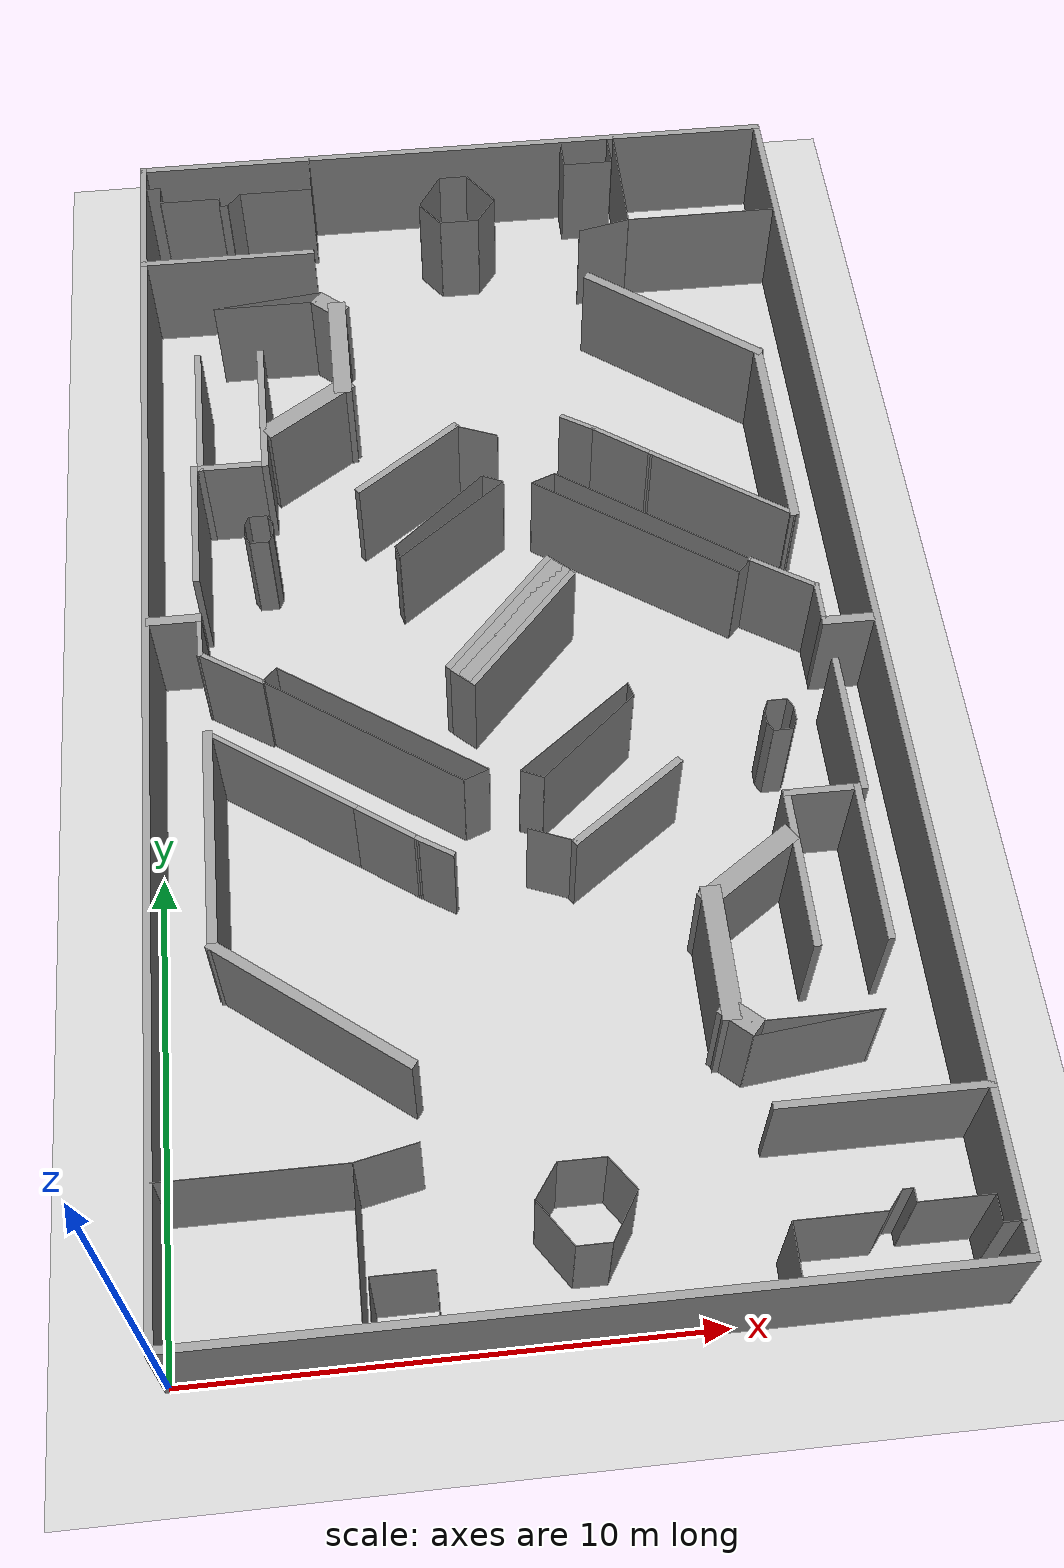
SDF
<sdf version="1.7">
 <world name="default">
  <light name="sun" type="directional">
   <pose>0 0 10 0 -0 0</pose>
   <diffuse>0.8 0.8 0.8 1</diffuse>
   <specular>0.2 0.2 0.2 1</specular>
   <attenuation>
    <range>1000</range>
    <constant>0.9</constant>
    <linear>0.01</linear>
    <quadratic>0.001</quadratic>
   </attenuation>
   <direction>-0.5 0.1 -0.9</direction>
   <spot><inner_angle>0</inner_angle><outer_angle>0</outer_angle><falloff>0</falloff></spot>
  </light>
  <model name="ground_plane">
   <static>1</static>
   <link name="link">
    <collision name="collision">
     <geometry><plane><normal>0 0 1</normal><size>100 100</size></plane></geometry>
     <surface>
      <contact><collide_bitmask>65535</collide_bitmask></contact>
      <friction><ode><mu>100</mu><mu2>50</mu2></ode></friction>
     </surface>
    </collision>
    <visual name="visual">
     <cast_shadows>0</cast_shadows>
     <geometry><plane><normal>0 0 1</normal><size>100 100</size></plane></geometry>
     <material>
      <script><uri>file://media/materials/scripts/gazebo.material</uri><name>Gazebo/Grey</name></script>
     </material>
    </visual>
   </link>
  </model>
  <gravity>0 0 -9.8</gravity>
  <magnetic_field>6e-06 2.3e-05 -4.2e-05</magnetic_field>
  <atmosphere type="adiabatic"/>
  <physics type="ode">
   <max_step_size>0.001</max_step_size>
   <real_time_factor>1</real_time_factor>
   <real_time_update_rate>1000</real_time_update_rate>
  </physics>
  <scene><ambient>0.4 0.4 0.4 1</ambient><background>0.7 0.7 0.7 1</background><shadows>1</shadows></scene>
  <spherical_coordinates>
   <surface_model>EARTH_WGS84</surface_model>
   <latitude_deg>0</latitude_deg>
   <longitude_deg>0</longitude_deg>
   <elevation>0</elevation>
   <heading_deg>0</heading_deg>
  </spherical_coordinates>
  <model name="Untitled">
   <pose>7.5 14 0 0 -0 0</pose>
   <link name="Wall_0">
    <collision name="Wall_0_Collision">
     <geometry><box><size>28.15 0.15 2.5</size></box></geometry>
     <pose>0 0 1.25 0 -0 0</pose>
    </collision>
    <visual name="Wall_0_Visual">
     <pose>0 0 1.25 0 -0 0</pose>
     <geometry><box><size>28.15 0.15 2.5</size></box></geometry>
     <material>
      <script><uri>file://media/materials/scripts/gazebo.material</uri><name>Gazebo/Grey</name></script>
      <ambient>1 1 1 1</ambient>
     </material>
     <meta><layer>0</layer></meta>
    </visual>
    <pose>-7.5 0 0 0 -0 1.5708</pose>
   </link>
   <link name="Wall_2">
    <collision name="Wall_2_Collision">
     <geometry><box><size>15.15 0.15 2.5</size></box></geometry>
     <pose>0 0 1.25 0 -0 0</pose>
    </collision>
    <visual name="Wall_2_Visual">
     <pose>0 0 1.25 0 -0 0</pose>
     <geometry><box><size>15.15 0.15 2.5</size></box></geometry>
     <material>
      <script><uri>file://media/materials/scripts/gazebo.material</uri><name>Gazebo/Grey</name></script>
      <ambient>1 1 1 1</ambient>
     </material>
     <meta><layer>0</layer></meta>
    </visual>
    <pose>-0 -14 0 0 -0 0</pose>
   </link>
   <link name="Wall_4">
    <collision name="Wall_4_Collision">
     <geometry><box><size>28.15 0.15 2.5</size></box></geometry>
     <pose>0 0 1.25 0 -0 0</pose>
    </collision>
    <visual name="Wall_4_Visual">
     <pose>0 0 1.25 0 -0 0</pose>
     <geometry><box><size>28.15 0.15 2.5</size></box></geometry>
     <material>
      <script><uri>file://media/materials/scripts/gazebo.material</uri><name>Gazebo/Grey</name></script>
      <ambient>1 1 1 1</ambient>
     </material>
     <meta><layer>0</layer></meta>
    </visual>
    <pose>7.5 0 0 0 -0 1.5708</pose>
   </link>
   <link name="Wall_6">
    <collision name="Wall_6_Collision">
     <geometry><box><size>15.15 0.15 2.5</size></box></geometry>
     <pose>0 0 1.25 0 -0 0</pose>
    </collision>
    <visual name="Wall_6_Visual">
     <pose>0 0 1.25 0 -0 0</pose>
     <geometry><box><size>15.15 0.15 2.5</size></box></geometry>
     <material>
      <script><uri>file://media/materials/scripts/gazebo.material</uri><name>Gazebo/Grey</name></script>
      <ambient>1 1 1 1</ambient>
     </material>
     <meta><layer>0</layer></meta>
    </visual>
    <pose>-0 14 0 0 -0 0</pose>
   </link>
   <static>1</static>
  </model>
  <model name="Untitled_0">
   <pose>4.22599 1.55046 0 0 -0 0</pose>
   <link name="Wall_0">
    <collision name="Wall_0_Collision">
     <geometry><box><size>3.56 0.01 2.5</size></box></geometry>
     <pose>0 0 1.25 0 -0 0</pose>
    </collision>
    <visual name="Wall_0_Visual">
     <pose>0 0 1.25 0 -0 0</pose>
     <geometry><box><size>3.56 0.01 2.5</size></box></geometry>
     <material>
      <script><uri>file://media/materials/scripts/gazebo.material</uri><name>Gazebo/Grey</name></script>
      <ambient>1 1 1 1</ambient>
     </material>
     <meta><layer>0</layer></meta>
    </visual>
    <pose>-2.45099 1.29954 0 0 -0 0</pose>
   </link>
   <link name="Wall_10">
    <collision name="Wall_10_Collision">
     <geometry><box><size>0.855 0.01 2.5</size></box></geometry>
     <pose>0 0 1.25 0 -0 0</pose>
    </collision>
    <visual name="Wall_10_Visual">
     <pose>0 0 1.25 0 -0 0</pose>
     <geometry><box><size>0.855 0.01 2.5</size></box></geometry>
     <material>
      <script><uri>file://media/materials/scripts/gazebo.material</uri><name>Gazebo/Grey</name></script>
      <ambient>1 1 1 1</ambient>
     </material>
     <meta><layer>0</layer></meta>
    </visual>
    <pose>0.624012 -1.12796 0 0 -0 -1.5708</pose>
   </link>
   <link name="Wall_12">
    <collision name="Wall_12_Collision">
     <geometry><box><size>0.91 0.01 2.5</size></box></geometry>
     <pose>0 0 1.25 0 -0 0</pose>
    </collision>
    <visual name="Wall_12_Visual">
     <pose>0 0 1.25 0 -0 0</pose>
     <geometry><box><size>0.91 0.01 2.5</size></box></geometry>
     <material>
      <script><uri>file://media/materials/scripts/gazebo.material</uri><name>Gazebo/Grey</name></script>
      <ambient>1 1 1 1</ambient>
     </material>
     <meta><layer>0</layer></meta>
    </visual>
    <pose>3.32401 0.949543 0 0 -0 0</pose>
   </link>
   <link name="Wall_14">
    <collision name="Wall_14_Collision">
     <geometry><box><size>0.784209 0.01 2.5</size></box></geometry>
     <pose>0 0 1.25 0 -0 0</pose>
    </collision>
    <visual name="Wall_14_Visual">
     <pose>0 0 1.25 0 -0 0</pose>
     <geometry><box><size>0.784209 0.01 2.5</size></box></geometry>
     <material>
      <script><uri>file://media/materials/scripts/gazebo.material</uri><name>Gazebo/Grey</name></script>
      <ambient>1 1 1 1</ambient>
     </material>
     <meta><layer>0</layer></meta>
    </visual>
    <pose>3.99901 0.634543 0 0 -0 -0.950547</pose>
   </link>
   <link name="Wall_16">
    <collision name="Wall_16_Collision">
     <geometry><box><size>1.03927 0.01 2.5</size></box></geometry>
     <pose>0 0 1.25 0 -0 0</pose>
    </collision>
    <visual name="Wall_16_Visual">
     <pose>0 0 1.25 0 -0 0</pose>
     <geometry><box><size>1.03927 0.01 2.5</size></box></geometry>
     <material>
      <script><uri>file://media/materials/scripts/gazebo.material</uri><name>Gazebo/Grey</name></script>
      <ambient>1 1 1 1</ambient>
     </material>
     <meta><layer>0</layer></meta>
    </visual>
    <pose>3.94901 -0.115457 0 0 -0 -2.13455</pose>
   </link>
   <link name="Wall_18">
    <collision name="Wall_18_Collision">
     <geometry><box><size>0.66 0.01 2.5</size></box></geometry>
     <pose>0 0 1.25 0 -0 0</pose>
    </collision>
    <visual name="Wall_18_Visual">
     <pose>0 0 1.25 0 -0 0</pose>
     <geometry><box><size>0.66 0.01 2.5</size></box></geometry>
     <material>
      <script><uri>file://media/materials/scripts/gazebo.material</uri><name>Gazebo/Grey</name></script>
      <ambient>1 1 1 1</ambient>
     </material>
     <meta><layer>0</layer></meta>
    </visual>
    <pose>3.34901 -0.550457 0 0 -0 3.14159</pose>
   </link>
   <link name="Wall_2">
    <collision name="Wall_2_Collision">
     <geometry><box><size>2.86 0.01 2.5</size></box></geometry>
     <pose>0 0 1.25 0 -0 0</pose>
    </collision>
    <visual name="Wall_2_Visual">
     <pose>0 0 1.25 0 -0 0</pose>
     <geometry><box><size>2.86 0.01 2.5</size></box></geometry>
     <material>
      <script><uri>file://media/materials/scripts/gazebo.material</uri><name>Gazebo/Grey</name></script>
      <ambient>1 1 1 1</ambient>
     </material>
     <meta><layer>0</layer></meta>
    </visual>
    <pose>-0.675988 -0.125457 0 0 -0 -1.5708</pose>
   </link>
   <link name="Wall_20">
    <collision name="Wall_20_Collision">
     <geometry><box><size>1.06683 0.01 2.5</size></box></geometry>
     <pose>0 0 1.25 0 -0 0</pose>
    </collision>
    <visual name="Wall_20_Visual">
     <pose>0 0 1.25 0 -0 0</pose>
     <geometry><box><size>1.06683 0.01 2.5</size></box></geometry>
     <material>
      <script><uri>file://media/materials/scripts/gazebo.material</uri><name>Gazebo/Grey</name></script>
      <ambient>1 1 1 1</ambient>
     </material>
     <meta><layer>0</layer></meta>
    </visual>
    <pose>2.72401 -0.115457 0 0 -0 2.17455</pose>
   </link>
   <link name="Wall_22">
    <collision name="Wall_22_Collision">
     <geometry><box><size>0.784209 0.01 2.5</size></box></geometry>
     <pose>0 0 1.25 0 -0 0</pose>
    </collision>
    <visual name="Wall_22_Visual">
     <pose>0 0 1.25 0 -0 0</pose>
     <geometry><box><size>0.784209 0.01 2.5</size></box></geometry>
     <material>
      <script><uri>file://media/materials/scripts/gazebo.material</uri><name>Gazebo/Grey</name></script>
      <ambient>1 1 1 1</ambient>
     </material>
     <meta><layer>0</layer></meta>
    </visual>
    <pose>2.64901 0.634543 0 0 -0 -2.19105</pose>
   </link>
   <link name="Wall_4">
    <collision name="Wall_4_Collision">
     <geometry><box><size>1.23577 0.01 2.5</size></box></geometry>
     <pose>0 0 1.25 0 -0 0</pose>
    </collision>
    <visual name="Wall_4_Visual">
     <pose>0 0 1.25 0 -0 0</pose>
     <geometry><box><size>1.23577 0.01 2.5</size></box></geometry>
     <material>
      <script><uri>file://media/materials/scripts/gazebo.material</uri><name>Gazebo/Grey</name></script>
      <ambient>1 1 1 1</ambient>
     </material>
     <meta><layer>0</layer></meta>
    </visual>
    <pose>-0.075987 1.42454 0 0 -0 0.205395</pose>
   </link>
   <link name="Wall_6">
    <collision name="Wall_6_Collision">
     <geometry><box><size>0.855 0.01 2.5</size></box></geometry>
     <pose>0 0 1.25 0 -0 0</pose>
    </collision>
    <visual name="Wall_6_Visual">
     <pose>0 0 1.25 0 -0 0</pose>
     <geometry><box><size>0.855 0.01 2.5</size></box></geometry>
     <material>
      <script><uri>file://media/materials/scripts/gazebo.material</uri><name>Gazebo/Grey</name></script>
      <ambient>1 1 1 1</ambient>
     </material>
     <meta><layer>0</layer></meta>
    </visual>
    <pose>-0.525987 -1.12796 0 0 -0 -1.5708</pose>
   </link>
   <link name="Wall_8">
    <collision name="Wall_8_Collision">
     <geometry><box><size>1.16 0.01 2.5</size></box></geometry>
     <pose>0 0 1.25 0 -0 0</pose>
    </collision>
    <visual name="Wall_8_Visual">
     <pose>0 0 1.25 0 -0 0</pose>
     <geometry><box><size>1.16 0.01 2.5</size></box></geometry>
     <material>
      <script><uri>file://media/materials/scripts/gazebo.material</uri><name>Gazebo/Grey</name></script>
      <ambient>1 1 1 1</ambient>
     </material>
     <meta><layer>0</layer></meta>
    </visual>
    <pose>0.049013 -0.705457 0 0 -0 0</pose>
   </link>
   <static>1</static>
  </model>
  <model name="Untitled_1">
   <pose>7.535 1.5925 0 0 -0 0</pose>
   <link name="Wall_0">
    <collision name="Wall_0_Collision">
     <geometry><box><size>1.06 0.01 2.5</size></box></geometry>
     <pose>0 0 1.25 0 -0 0</pose>
    </collision>
    <visual name="Wall_0_Visual">
     <pose>0 0 1.25 0 -0 0</pose>
     <geometry><box><size>1.06 0.01 2.5</size></box></geometry>
     <material>
      <script><uri>file://media/materials/scripts/gazebo.material</uri><name>Gazebo/Grey</name></script>
      <ambient>1 1 1 1</ambient>
     </material>
     <meta><layer>0</layer></meta>
    </visual>
    <pose>3.465 -1.0675 0 0 -0 1.5708</pose>
   </link>
   <link name="Wall_10">
    <collision name="Wall_10_Collision">
     <geometry><box><size>0.470977 0.01 2.5</size></box></geometry>
     <pose>0 0 1.25 0 -0 0</pose>
    </collision>
    <visual name="Wall_10_Visual">
     <pose>0 0 1.25 0 -0 0</pose>
     <geometry><box><size>0.470977 0.01 2.5</size></box></geometry>
     <material>
      <script><uri>file://media/materials/scripts/gazebo.material</uri><name>Gazebo/Grey</name></script>
      <ambient>1 1 1 1</ambient>
     </material>
     <meta><layer>0</layer></meta>
    </visual>
    <pose>5.315 -0.3675 0 0 -0 0.86217</pose>
   </link>
   <link name="Wall_14">
    <collision name="Wall_14_Collision">
     <geometry><box><size>0.01 0.01 2.5</size></box></geometry>
     <pose>0 0 1.25 0 -0 0</pose>
    </collision>
    <visual name="Wall_14_Visual">
     <pose>0 0 1.25 0 -0 0</pose>
     <geometry><box><size>0.01 0.01 2.5</size></box></geometry>
     <material>
      <script><uri>file://media/materials/scripts/gazebo.material</uri><name>Gazebo/Grey</name></script>
      <ambient>1 1 1 1</ambient>
     </material>
     <meta><layer>0</layer></meta>
    </visual>
    <pose>5.465 -0.1925 0 0 -0 0</pose>
   </link>
   <link name="Wall_18">
    <collision name="Wall_18_Collision">
     <geometry><box><size>0.01 0.01 2.5</size></box></geometry>
     <pose>0 0 1.25 0 -0 0</pose>
    </collision>
    <visual name="Wall_18_Visual">
     <pose>0 0 1.25 0 -0 0</pose>
     <geometry><box><size>0.01 0.01 2.5</size></box></geometry>
     <material>
      <script><uri>file://media/materials/scripts/gazebo.material</uri><name>Gazebo/Grey</name></script>
      <ambient>1 1 1 1</ambient>
     </material>
     <meta><layer>0</layer></meta>
    </visual>
    <pose>5.665 -0.1925 0 0 -0 0</pose>
   </link>
   <link name="Wall_20">
    <collision name="Wall_20_Collision">
     <geometry><box><size>0.26 0.01 2.5</size></box></geometry>
     <pose>0 0 1.25 0 -0 0</pose>
    </collision>
    <visual name="Wall_20_Visual">
     <pose>0 0 1.25 0 -0 0</pose>
     <geometry><box><size>0.26 0.01 2.5</size></box></geometry>
     <material>
      <script><uri>file://media/materials/scripts/gazebo.material</uri><name>Gazebo/Grey</name></script>
      <ambient>1 1 1 1</ambient>
     </material>
     <meta><layer>0</layer></meta>
    </visual>
    <pose>5.665 -0.3175 0 0 -0 -1.5708</pose>
   </link>
   <link name="Wall_22">
    <collision name="Wall_22_Collision">
     <geometry><box><size>0.21 0.01 2.5</size></box></geometry>
     <pose>0 0 1.25 0 -0 0</pose>
    </collision>
    <visual name="Wall_22_Visual">
     <pose>0 0 1.25 0 -0 0</pose>
     <geometry><box><size>0.21 0.01 2.5</size></box></geometry>
     <material>
      <script><uri>file://media/materials/scripts/gazebo.material</uri><name>Gazebo/Grey</name></script>
      <ambient>1 1 1 1</ambient>
     </material>
     <meta><layer>0</layer></meta>
    </visual>
    <pose>5.565 -0.1925 0 0 -0 0</pose>
   </link>
   <link name="Wall_24">
    <collision name="Wall_24_Collision">
     <geometry><box><size>1.41 0.01 2.5</size></box></geometry>
     <pose>0 0 1.25 0 -0 0</pose>
    </collision>
    <visual name="Wall_24_Visual">
     <pose>0 0 1.25 0 -0 0</pose>
     <geometry><box><size>1.41 0.01 2.5</size></box></geometry>
     <material>
      <script><uri>file://media/materials/scripts/gazebo.material</uri><name>Gazebo/Grey</name></script>
      <ambient>1 1 1 1</ambient>
     </material>
     <meta><layer>0</layer></meta>
    </visual>
    <pose>6.365 -0.4425 0 0 -0 0</pose>
   </link>
   <link name="Wall_26">
    <collision name="Wall_26_Collision">
     <geometry><box><size>0.512 0.01 2.5</size></box></geometry>
     <pose>0 0 1.25 0 -0 0</pose>
    </collision>
    <visual name="Wall_26_Visual">
     <pose>0 0 1.25 0 -0 0</pose>
     <geometry><box><size>0.512 0.01 2.5</size></box></geometry>
     <material>
      <script><uri>file://media/materials/scripts/gazebo.material</uri><name>Gazebo/Grey</name></script>
      <ambient>1 1 1 1</ambient>
     </material>
     <meta><layer>0</layer></meta>
    </visual>
    <pose>7.065 -0.6935 0 0 -0 -1.5708</pose>
   </link>
   <link name="Wall_28">
    <collision name="Wall_28_Collision">
     <geometry><box><size>0.41 0.01 2.5</size></box></geometry>
     <pose>0 0 1.25 0 -0 0</pose>
    </collision>
    <visual name="Wall_28_Visual">
     <pose>0 0 1.25 0 -0 0</pose>
     <geometry><box><size>0.41 0.01 2.5</size></box></geometry>
     <material>
      <script><uri>file://media/materials/scripts/gazebo.material</uri><name>Gazebo/Grey</name></script>
      <ambient>1 1 1 1</ambient>
     </material>
     <meta><layer>0</layer></meta>
    </visual>
    <pose>7.265 -0.9445 0 0 -0 0</pose>
   </link>
   <link name="Wall_30">
    <collision name="Wall_30_Collision">
     <geometry><box><size>4.04 0.14 2.5</size></box></geometry>
     <pose>0 0 1.25 0 -0 0</pose>
    </collision>
    <visual name="Wall_30_Visual">
     <pose>0 0 1.25 0 -0 0</pose>
     <geometry><box><size>4.04 0.14 2.5</size></box></geometry>
     <material>
      <script><uri>file://media/materials/scripts/gazebo.material</uri><name>Gazebo/Grey</name></script>
      <ambient>1 1 1 1</ambient>
     </material>
     <meta><layer>0</layer></meta>
    </visual>
    <pose>5.515 1.5275 0 0 -0 0</pose>
   </link>
   <link name="Wall_8">
    <collision name="Wall_8_Collision">
     <geometry><box><size>1.71 0.01 2.5</size></box></geometry>
     <pose>0 0 1.25 0 -0 0</pose>
    </collision>
    <visual name="Wall_8_Visual">
     <pose>0 0 1.25 0 -0 0</pose>
     <geometry><box><size>1.71 0.01 2.5</size></box></geometry>
     <material>
      <script><uri>file://media/materials/scripts/gazebo.material</uri><name>Gazebo/Grey</name></script>
      <ambient>1 1 1 1</ambient>
     </material>
     <meta><layer>0</layer></meta>
    </visual>
    <pose>4.315 -0.5425 0 0 -0 0</pose>
   </link>
   <static>1</static>
  </model>
  <model name="Untitled_2">
   <pose>7.005 6.18515 0 0 -0 0</pose>
   <link name="Wall_0">
    <collision name="Wall_0_Collision">
     <geometry><box><size>2.73 0.4 2.5</size></box></geometry>
     <pose>0 0 1.25 0 -0 0</pose>
    </collision>
    <visual name="Wall_0_Visual">
     <pose>0 0 1.25 0 -0 0</pose>
     <geometry><box><size>2.73 0.4 2.5</size></box></geometry>
     <material>
      <script><uri>file://media/materials/scripts/gazebo.material</uri><name>Gazebo/Grey</name></script>
      <ambient>1 1 1 1</ambient>
     </material>
     <meta><layer>0</layer></meta>
    </visual>
    <pose>3.595 -0.020154 0 0 -0 -1.5708</pose>
   </link>
   <link name="Wall_10">
    <collision name="Wall_10_Collision">
     <geometry><box><size>3.36 0.15 2.5</size></box></geometry>
     <pose>0 0 1.25 0 -0 0</pose>
    </collision>
    <visual name="Wall_10_Visual">
     <pose>0 0 1.25 0 -0 0</pose>
     <geometry><box><size>3.36 0.15 2.5</size></box></geometry>
     <material>
      <script><uri>file://media/materials/scripts/gazebo.material</uri><name>Gazebo/Grey</name></script>
      <ambient>1 1 1 1</ambient>
     </material>
     <meta><layer>0</layer></meta>
    </visual>
    <pose>5.395 1.57985 0 0 -0 1.5708</pose>
   </link>
   <link name="Wall_12">
    <collision name="Wall_12_Collision">
     <geometry><box><size>1.54 0.14 2.5</size></box></geometry>
     <pose>0 0 1.25 0 -0 0</pose>
    </collision>
    <visual name="Wall_12_Visual">
     <pose>0 0 1.25 0 -0 0</pose>
     <geometry><box><size>1.54 0.14 2.5</size></box></geometry>
     <material>
      <script><uri>file://media/materials/scripts/gazebo.material</uri><name>Gazebo/Grey</name></script>
      <ambient>1 1 1 1</ambient>
     </material>
     <meta><layer>0</layer></meta>
    </visual>
    <pose>6.095 3.18485 0 0 -0 0</pose>
   </link>
   <link name="Wall_14">
    <collision name="Wall_14_Collision">
     <geometry><box><size>3.35 0.14 2.5</size></box></geometry>
     <pose>0 0 1.25 0 -0 0</pose>
    </collision>
    <visual name="Wall_14_Visual">
     <pose>0 0 1.25 0 -0 0</pose>
     <geometry><box><size>3.35 0.14 2.5</size></box></geometry>
     <material>
      <script><uri>file://media/materials/scripts/gazebo.material</uri><name>Gazebo/Grey</name></script>
      <ambient>1 1 1 1</ambient>
     </material>
     <meta><layer>0</layer></meta>
    </visual>
    <pose>6.795 1.57985 0 0 -0 -1.5708</pose>
   </link>
   <link name="Wall_16">
    <collision name="Wall_16_Collision">
     <geometry><box><size>3.07061 0.14 2.5</size></box></geometry>
     <pose>0 0 1.25 0 -0 0</pose>
    </collision>
    <visual name="Wall_16_Visual">
     <pose>0 0 1.25 0 -0 0</pose>
     <geometry><box><size>3.07061 0.14 2.5</size></box></geometry>
     <material>
      <script><uri>file://media/materials/scripts/gazebo.material</uri><name>Gazebo/Grey</name></script>
      <ambient>1 1 1 1</ambient>
     </material>
     <meta><layer>0</layer></meta>
    </visual>
    <pose>6.935 4.64985 0 0 -0 1.5708</pose>
   </link>
   <link name="Wall_2">
    <collision name="Wall_2_Collision">
     <geometry><box><size>0.803609 0.4 2.5</size></box></geometry>
     <pose>0 0 1.25 0 -0 0</pose>
    </collision>
    <visual name="Wall_2_Visual">
     <pose>0 0 1.25 0 -0 0</pose>
     <geometry><box><size>0.803609 0.4 2.5</size></box></geometry>
     <material>
      <script><uri>file://media/materials/scripts/gazebo.material</uri><name>Gazebo/Grey</name></script>
      <ambient>1 1 1 1</ambient>
     </material>
     <meta><layer>0</layer></meta>
    </visual>
    <pose>3.745 -1.32015 0 0 -0 -0.732815</pose>
   </link>
   <link name="Wall_4">
    <collision name="Wall_4_Collision">
     <geometry><box><size>2.51 0.01 2.5</size></box></geometry>
     <pose>0 0 1.25 0 -0 0</pose>
    </collision>
    <visual name="Wall_4_Visual">
     <pose>0 0 1.25 0 -0 0</pose>
     <geometry><box><size>2.51 0.01 2.5</size></box></geometry>
     <material>
      <script><uri>file://media/materials/scripts/gazebo.material</uri><name>Gazebo/Grey</name></script>
      <ambient>1 1 1 1</ambient>
     </material>
     <meta><layer>0</layer></meta>
    </visual>
    <pose>5.145 -1.45515 0 0 -0 0</pose>
   </link>
   <link name="Wall_6">
    <collision name="Wall_6_Collision">
     <geometry><box><size>2.51563 0.001 2.5</size></box></geometry>
     <pose>0 0 1.25 0 -0 0</pose>
    </collision>
    <visual name="Wall_6_Visual">
     <pose>0 0 1.25 0 -0 0</pose>
     <geometry><box><size>2.51563 0.001 2.5</size></box></geometry>
     <material>
      <script><uri>file://media/materials/scripts/gazebo.material</uri><name>Gazebo/Grey</name></script>
      <ambient>1 1 1 1</ambient>
     </material>
     <meta><layer>0</layer></meta>
    </visual>
    <pose>5.145 -1.59515 0 0 -0 -3.03006</pose>
   </link>
   <link name="Wall_8">
    <collision name="Wall_8_Collision">
     <geometry><box><size>2.33039 0.4 2.5</size></box></geometry>
     <pose>0 0 1.25 0 -0 0</pose>
    </collision>
    <visual name="Wall_8_Visual">
     <pose>0 0 1.25 0 -0 0</pose>
     <geometry><box><size>2.33039 0.4 2.5</size></box></geometry>
     <material>
      <script><uri>file://media/materials/scripts/gazebo.material</uri><name>Gazebo/Grey</name></script>
      <ambient>1 1 1 1</ambient>
     </material>
     <meta><layer>0</layer></meta>
    </visual>
    <pose>4.395 1.68485 0 0 -0 0.59375</pose>
   </link>
   <static>1</static>
  </model>
  <model name="Untitled_3">
   <pose>6.45335 5.75335 0 0 -0 0</pose>
   <link name="Wall_0">
    <collision name="Wall_0_Collision">
     <geometry><box><size>0.233607 0.01 2.5</size></box></geometry>
     <pose>0 0 1.25 0 -0 0</pose>
    </collision>
    <visual name="Wall_0_Visual">
     <pose>0 0 1.25 0 -0 0</pose>
     <geometry><box><size>0.233607 0.01 2.5</size></box></geometry>
     <material>
      <script><uri>file://media/materials/scripts/gazebo.material</uri><name>Gazebo/Grey</name></script>
      <ambient>1 1 1 1</ambient>
     </material>
     <meta><layer>0</layer></meta>
    </visual>
    <pose>5.89665 5.64665 0 0 -0 -2.03444</pose>
   </link>
   <link name="Wall_10">
    <collision name="Wall_10_Collision">
     <geometry><box><size>0.31 0.01 2.5</size></box></geometry>
     <pose>0 0 1.25 0 -0 0</pose>
    </collision>
    <visual name="Wall_10_Visual">
     <pose>0 0 1.25 0 -0 0</pose>
     <geometry><box><size>0.31 0.01 2.5</size></box></geometry>
     <material>
      <script><uri>file://media/materials/scripts/gazebo.material</uri><name>Gazebo/Grey</name></script>
      <ambient>1 1 1 1</ambient>
     </material>
     <meta><layer>0</layer></meta>
    </visual>
    <pose>6.44665 5.39665 0 0 -0 1.5708</pose>
   </link>
   <link name="Wall_12">
    <collision name="Wall_12_Collision">
     <geometry><box><size>0.233607 0.01 2.5</size></box></geometry>
     <pose>0 0 1.25 0 -0 0</pose>
    </collision>
    <visual name="Wall_12_Visual">
     <pose>0 0 1.25 0 -0 0</pose>
     <geometry><box><size>0.233607 0.01 2.5</size></box></geometry>
     <material>
      <script><uri>file://media/materials/scripts/gazebo.material</uri><name>Gazebo/Grey</name></script>
      <ambient>1 1 1 1</ambient>
     </material>
     <meta><layer>0</layer></meta>
    </visual>
    <pose>6.39665 5.64665 0 0 -0 2.03444</pose>
   </link>
   <link name="Wall_14">
    <collision name="Wall_14_Collision">
     <geometry><box><size>0.41 0.01 2.5</size></box></geometry>
     <pose>0 0 1.25 0 -0 0</pose>
    </collision>
    <visual name="Wall_14_Visual">
     <pose>0 0 1.25 0 -0 0</pose>
     <geometry><box><size>0.41 0.01 2.5</size></box></geometry>
     <material>
      <script><uri>file://media/materials/scripts/gazebo.material</uri><name>Gazebo/Grey</name></script>
      <ambient>1 1 1 1</ambient>
     </material>
     <meta><layer>0</layer></meta>
    </visual>
    <pose>6.14665 5.74665 0 0 -0 0</pose>
   </link>
   <link name="Wall_2">
    <collision name="Wall_2_Collision">
     <geometry><box><size>0.31 0.01 2.5</size></box></geometry>
     <pose>0 0 1.25 0 -0 0</pose>
    </collision>
    <visual name="Wall_2_Visual">
     <pose>0 0 1.25 0 -0 0</pose>
     <geometry><box><size>0.31 0.01 2.5</size></box></geometry>
     <material>
      <script><uri>file://media/materials/scripts/gazebo.material</uri><name>Gazebo/Grey</name></script>
      <ambient>1 1 1 1</ambient>
     </material>
     <meta><layer>0</layer></meta>
    </visual>
    <pose>5.84665 5.39665 0 0 -0 -1.5708</pose>
   </link>
   <link name="Wall_4">
    <collision name="Wall_4_Collision">
     <geometry><box><size>0.233607 0.01 2.5</size></box></geometry>
     <pose>0 0 1.25 0 -0 0</pose>
    </collision>
    <visual name="Wall_4_Visual">
     <pose>0 0 1.25 0 -0 0</pose>
     <geometry><box><size>0.233607 0.01 2.5</size></box></geometry>
     <material>
      <script><uri>file://media/materials/scripts/gazebo.material</uri><name>Gazebo/Grey</name></script>
      <ambient>1 1 1 1</ambient>
     </material>
     <meta><layer>0</layer></meta>
    </visual>
    <pose>5.89665 5.14665 0 0 -0 -1.10715</pose>
   </link>
   <link name="Wall_6">
    <collision name="Wall_6_Collision">
     <geometry><box><size>0.41 0.01 2.5</size></box></geometry>
     <pose>0 0 1.25 0 -0 0</pose>
    </collision>
    <visual name="Wall_6_Visual">
     <pose>0 0 1.25 0 -0 0</pose>
     <geometry><box><size>0.41 0.01 2.5</size></box></geometry>
     <material>
      <script><uri>file://media/materials/scripts/gazebo.material</uri><name>Gazebo/Grey</name></script>
      <ambient>1 1 1 1</ambient>
     </material>
     <meta><layer>0</layer></meta>
    </visual>
    <pose>6.14665 5.04665 0 0 -0 0</pose>
   </link>
   <link name="Wall_8">
    <collision name="Wall_8_Collision">
     <geometry><box><size>0.233607 0.01 2.5</size></box></geometry>
     <pose>0 0 1.25 0 -0 0</pose>
    </collision>
    <visual name="Wall_8_Visual">
     <pose>0 0 1.25 0 -0 0</pose>
     <geometry><box><size>0.233607 0.01 2.5</size></box></geometry>
     <material>
      <script><uri>file://media/materials/scripts/gazebo.material</uri><name>Gazebo/Grey</name></script>
      <ambient>1 1 1 1</ambient>
     </material>
     <meta><layer>0</layer></meta>
    </visual>
    <pose>6.39665 5.14665 0 0 -0 1.10715</pose>
   </link>
   <static>1</static>
  </model>
  <model name="Untitled_4">
   <pose>5.25232 6.65353 0 0 -0 0</pose>
   <link name="Wall_0">
    <collision name="Wall_0_Collision">
     <geometry><box><size>2.83067 0.15 2.5</size></box></geometry>
     <pose>0 0 1.25 0 -0 0</pose>
    </collision>
    <visual name="Wall_0_Visual">
     <pose>0 0 1.25 0 -0 0</pose>
     <geometry><box><size>2.83067 0.15 2.5</size></box></geometry>
     <material>
      <script><uri>file://media/materials/scripts/gazebo.material</uri><name>Gazebo/Grey</name></script>
      <ambient>1 1 1 1</ambient>
     </material>
     <meta><layer>0</layer></meta>
    </visual>
    <pose>4.05768 2.86646 0 0 -0 -2.52048</pose>
   </link>
   <link name="Wall_10">
    <collision name="Wall_10_Collision">
     <geometry><box><size>2.63488 0.01 2.5</size></box></geometry>
     <pose>0 0 1.25 0 -0 0</pose>
    </collision>
    <visual name="Wall_10_Visual">
     <pose>0 0 1.25 0 -0 0</pose>
     <geometry><box><size>2.63488 0.01 2.5</size></box></geometry>
     <material>
      <script><uri>file://media/materials/scripts/gazebo.material</uri><name>Gazebo/Grey</name></script>
      <ambient>1 1 1 1</ambient>
     </material>
     <meta><layer>0</layer></meta>
    </visual>
    <pose>3.49768 4.39647 0 0 -0 0.704494</pose>
   </link>
   <link name="Wall_12">
    <collision name="Wall_12_Collision">
     <geometry><box><size>4.9419 0.01 2.5</size></box></geometry>
     <pose>0 0 1.25 0 -0 0</pose>
    </collision>
    <visual name="Wall_12_Visual">
     <pose>0 0 1.25 0 -0 0</pose>
     <geometry><box><size>4.9419 0.01 2.5</size></box></geometry>
     <material>
      <script><uri>file://media/materials/scripts/gazebo.material</uri><name>Gazebo/Grey</name></script>
      <ambient>1 1 1 1</ambient>
     </material>
     <meta><layer>0</layer></meta>
    </visual>
    <pose>-0.582319 5.24646 0 0 -0 -0.603749</pose>
   </link>
   <link name="Wall_14">
    <collision name="Wall_14_Collision">
     <geometry><box><size>0.434264 0.01 2.5</size></box></geometry>
     <pose>0 0 1.25 0 -0 0</pose>
    </collision>
    <visual name="Wall_14_Visual">
     <pose>0 0 1.25 0 -0 0</pose>
     <geometry><box><size>0.434264 0.01 2.5</size></box></geometry>
     <material>
      <script><uri>file://media/materials/scripts/gazebo.material</uri><name>Gazebo/Grey</name></script>
      <ambient>1 1 1 1</ambient>
     </material>
     <meta><layer>0</layer></meta>
    </visual>
    <pose>-2.76232 6.49646 0 0 -0 -2.35619</pose>
   </link>
   <link name="Wall_16">
    <collision name="Wall_16_Collision">
     <geometry><box><size>4.70421 0.01 2.5</size></box></geometry>
     <pose>0 0 1.25 0 -0 0</pose>
    </collision>
    <visual name="Wall_16_Visual">
     <pose>0 0 1.25 0 -0 0</pose>
     <geometry><box><size>4.70421 0.01 2.5</size></box></geometry>
     <material>
      <script><uri>file://media/materials/scripts/gazebo.material</uri><name>Gazebo/Grey</name></script>
      <ambient>1 1 1 1</ambient>
     </material>
     <meta><layer>0</layer></meta>
    </visual>
    <pose>-0.992319 4.99646 0 0 -0 -0.61282</pose>
   </link>
   <link name="Wall_18">
    <collision name="Wall_18_Collision">
     <geometry><box><size>0.567136 0.01 2.5</size></box></geometry>
     <pose>0 0 1.25 0 -0 0</pose>
    </collision>
    <visual name="Wall_18_Visual">
     <pose>0 0 1.25 0 -0 0</pose>
     <geometry><box><size>0.567136 0.01 2.5</size></box></geometry>
     <material>
      <script><uri>file://media/materials/scripts/gazebo.material</uri><name>Gazebo/Grey</name></script>
      <ambient>1 1 1 1</ambient>
     </material>
     <meta><layer>0</layer></meta>
    </visual>
    <pose>1.18768 3.74646 0 0 -0 0.367174</pose>
   </link>
   <link name="Wall_2">
    <collision name="Wall_2_Collision">
     <geometry><box><size>1.00161 0.01 2.5</size></box></geometry>
     <pose>0 0 1.25 0 -0 0</pose>
    </collision>
    <visual name="Wall_2_Visual">
     <pose>0 0 1.25 0 -0 0</pose>
     <geometry><box><size>1.00161 0.01 2.5</size></box></geometry>
     <material>
      <script><uri>file://media/materials/scripts/gazebo.material</uri><name>Gazebo/Grey</name></script>
      <ambient>1 1 1 1</ambient>
     </material>
     <meta><layer>0</layer></meta>
    </visual>
    <pose>2.50768 2.27147 0 0 -0 2.75921</pose>
   </link>
   <link name="Wall_20">
    <collision name="Wall_20_Collision">
     <geometry><box><size>0.502443 0.01 2.5</size></box></geometry>
     <pose>0 0 1.25 0 -0 0</pose>
    </collision>
    <visual name="Wall_20_Visual">
     <pose>0 0 1.25 0 -0 0</pose>
     <geometry><box><size>0.502443 0.01 2.5</size></box></geometry>
     <material>
      <script><uri>file://media/materials/scripts/gazebo.material</uri><name>Gazebo/Grey</name></script>
      <ambient>1 1 1 1</ambient>
     </material>
     <meta><layer>0</layer></meta>
    </visual>
    <pose>2.27268 3.64647 0 0 -0 2.72337</pose>
   </link>
   <link name="Wall_22">
    <collision name="Wall_22_Collision">
     <geometry><box><size>0.854718 0.1 2.5</size></box></geometry>
     <pose>0 0 1.25 0 -0 0</pose>
    </collision>
    <visual name="Wall_22_Visual">
     <pose>0 0 1.25 0 -0 0</pose>
     <geometry><box><size>0.854718 0.1 2.5</size></box></geometry>
     <material>
      <script><uri>file://media/materials/scripts/gazebo.material</uri><name>Gazebo/Grey</name></script>
      <ambient>1 1 1 1</ambient>
     </material>
     <meta><layer>0</layer></meta>
    </visual>
    <pose>0.247681 2.26647 0 0 -0 -0.558599</pose>
   </link>
   <link name="Wall_24">
    <collision name="Wall_24_Collision">
     <geometry><box><size>1.52056 0.1 2.5</size></box></geometry>
     <pose>0 0 1.25 0 -0 0</pose>
    </collision>
    <visual name="Wall_24_Visual">
     <pose>0 0 1.25 0 -0 0</pose>
     <geometry><box><size>1.52056 0.1 2.5</size></box></geometry>
     <material>
      <script><uri>file://media/materials/scripts/gazebo.material</uri><name>Gazebo/Grey</name></script>
      <ambient>1 1 1 1</ambient>
     </material>
     <meta><layer>0</layer></meta>
    </visual>
    <pose>-0.652319 2.87646 0 0 -0 -0.61534</pose>
   </link>
   <link name="Wall_26">
    <collision name="Wall_26_Collision">
     <geometry><box><size>3.52603 0.1 2.5</size></box></geometry>
     <pose>0 0 1.25 0 -0 0</pose>
    </collision>
    <visual name="Wall_26_Visual">
     <pose>0 0 1.25 0 -0 0</pose>
     <geometry><box><size>3.52603 0.1 2.5</size></box></geometry>
     <material>
      <script><uri>file://media/materials/scripts/gazebo.material</uri><name>Gazebo/Grey</name></script>
      <ambient>1 1 1 1</ambient>
     </material>
     <meta><layer>0</layer></meta>
    </visual>
    <pose>-2.63732 4.26647 0 0 -0 -0.609052</pose>
   </link>
   <link name="Wall_6">
    <collision name="Wall_6_Collision">
     <geometry><box><size>0.320483 0.01 2.5</size></box></geometry>
     <pose>0 0 1.25 0 -0 0</pose>
    </collision>
    <visual name="Wall_6_Visual">
     <pose>0 0 1.25 0 -0 0</pose>
     <geometry><box><size>0.320483 0.01 2.5</size></box></geometry>
     <material>
      <script><uri>file://media/materials/scripts/gazebo.material</uri><name>Gazebo/Grey</name></script>
      <ambient>1 1 1 1</ambient>
     </material>
     <meta><layer>0</layer></meta>
    </visual>
    <pose>4.45768 5.39647 0 0 -0 -1.31019</pose>
   </link>
   <link name="Wall_8">
    <collision name="Wall_8_Collision">
     <geometry><box><size>2.98605 0.01 2.5</size></box></geometry>
     <pose>0 0 1.25 0 -0 0</pose>
    </collision>
    <visual name="Wall_8_Visual">
     <pose>0 0 1.25 0 -0 0</pose>
     <geometry><box><size>2.98605 0.01 2.5</size></box></geometry>
     <material>
      <script><uri>file://media/materials/scripts/gazebo.material</uri><name>Gazebo/Grey</name></script>
      <ambient>1 1 1 1</ambient>
     </material>
     <meta><layer>0</layer></meta>
    </visual>
    <pose>3.23268 4.64647 0 0 -0 0.649549</pose>
   </link>
   <static>1</static>
  </model>
  <model name="Untitled_5">
   <pose>4.47754 7.72254 0 0 -0 0</pose>
   <link name="Wall_10">
    <collision name="Wall_10_Collision">
     <geometry><box><size>4.79 0.2 2.5</size></box></geometry>
     <pose>0 0 1.25 0 -0 0</pose>
    </collision>
    <visual name="Wall_10_Visual">
     <pose>0 0 1.25 0 -0 0</pose>
     <geometry><box><size>4.79 0.2 2.5</size></box></geometry>
     <material>
      <script><uri>file://media/materials/scripts/gazebo.material</uri><name>Gazebo/Grey</name></script>
      <ambient>1 1 1 1</ambient>
     </material>
     <meta><layer>0</layer></meta>
    </visual>
    <pose>-3.26754 1.83246 0 0 -0 -1.5708</pose>
   </link>
   <link name="Wall_12">
    <collision name="Wall_12_Collision">
     <geometry><box><size>4.5942 0.2 2.5</size></box></geometry>
     <pose>0 0 1.25 0 -0 0</pose>
    </collision>
    <visual name="Wall_12_Visual">
     <pose>0 0 1.25 0 -0 0</pose>
     <geometry><box><size>4.5942 0.2 2.5</size></box></geometry>
     <material>
      <script><uri>file://media/materials/scripts/gazebo.material</uri><name>Gazebo/Grey</name></script>
      <ambient>1 1 1 1</ambient>
     </material>
     <meta><layer>0</layer></meta>
    </visual>
    <pose>-1.52254 -1.79754 0 0 -0 -0.653059</pose>
   </link>
   <link name="Wall_14">
    <collision name="Wall_14_Collision">
     <geometry><box><size>3.48217 0.63 2.5</size></box></geometry>
     <pose>0 0 1.25 0 -0 0</pose>
    </collision>
    <visual name="Wall_14_Visual">
     <pose>0 0 1.25 0 -0 0</pose>
     <geometry><box><size>3.48217 0.63 2.5</size></box></geometry>
     <material>
      <script><uri>file://media/materials/scripts/gazebo.material</uri><name>Gazebo/Grey</name></script>
      <ambient>1 1 1 1</ambient>
     </material>
     <meta><layer>0</layer></meta>
    </visual>
    <pose>3.06746 6.22746 0 0 -0 -2.31404</pose>
   </link>
   <link name="Wall_4">
    <collision name="Wall_4_Collision">
     <geometry><box><size>1.57567 0.1 2.5</size></box></geometry>
     <pose>0 0 1.25 0 -0 0</pose>
    </collision>
    <visual name="Wall_4_Visual">
     <pose>0 0 1.25 0 -0 0</pose>
     <geometry><box><size>1.57567 0.1 2.5</size></box></geometry>
     <material>
      <script><uri>file://media/materials/scripts/gazebo.material</uri><name>Gazebo/Grey</name></script>
      <ambient>1 1 1 1</ambient>
     </material>
     <meta><layer>0</layer></meta>
    </visual>
    <pose>-2.75754 5.67746 0 0 -0 -0.572966</pose>
   </link>
   <link name="Wall_6">
    <collision name="Wall_6_Collision">
     <geometry><box><size>1 0.1 2.5</size></box></geometry>
     <pose>0 0 1.25 0 -0 0</pose>
    </collision>
    <visual name="Wall_6_Visual">
     <pose>0 0 1.25 0 -0 0</pose>
     <geometry><box><size>1 0.1 2.5</size></box></geometry>
     <material>
      <script><uri>file://media/materials/scripts/gazebo.material</uri><name>Gazebo/Grey</name></script>
      <ambient>1 1 1 1</ambient>
     </material>
     <meta><layer>0</layer></meta>
    </visual>
    <pose>-3.37754 6.52746 0 0 -0 1.5708</pose>
   </link>
   <link name="Wall_8">
    <collision name="Wall_8_Collision">
     <geometry><box><size>1.15 0.2 2.5</size></box></geometry>
     <pose>0 0 1.25 0 -0 0</pose>
    </collision>
    <visual name="Wall_8_Visual">
     <pose>0 0 1.25 0 -0 0</pose>
     <geometry><box><size>1.15 0.2 2.5</size></box></geometry>
     <material>
      <script><uri>file://media/materials/scripts/gazebo.material</uri><name>Gazebo/Grey</name></script>
      <ambient>1 1 1 1</ambient>
     </material>
     <meta><layer>0</layer></meta>
    </visual>
    <pose>-3.90254 6.97746 0 0 -0 0</pose>
   </link>
   <static>1</static>
  </model>
  <model name="Untitled_0_clone">
   <pose>10.7704 26.4495 0 0 0 -3.14159</pose>
   <link name="Wall_0">
    <collision name="Wall_0_Collision">
     <geometry><box><size>3.56 0.01 2.5</size></box></geometry>
     <pose>0 0 1.25 0 -0 0</pose>
    </collision>
    <visual name="Wall_0_Visual">
     <pose>0 0 1.25 0 -0 0</pose>
     <geometry><box><size>3.56 0.01 2.5</size></box></geometry>
     <material>
      <script><uri>file://media/materials/scripts/gazebo.material</uri><name>Gazebo/Grey</name></script>
      <ambient>1 1 1 1</ambient>
     </material>
     <meta><layer>0</layer></meta>
    </visual>
    <pose>-2.45099 1.29954 0 0 -0 0</pose>
   </link>
   <link name="Wall_10">
    <collision name="Wall_10_Collision">
     <geometry><box><size>0.855 0.01 2.5</size></box></geometry>
     <pose>0 0 1.25 0 -0 0</pose>
    </collision>
    <visual name="Wall_10_Visual">
     <pose>0 0 1.25 0 -0 0</pose>
     <geometry><box><size>0.855 0.01 2.5</size></box></geometry>
     <material>
      <script><uri>file://media/materials/scripts/gazebo.material</uri><name>Gazebo/Grey</name></script>
      <ambient>1 1 1 1</ambient>
     </material>
     <meta><layer>0</layer></meta>
    </visual>
    <pose>0.624012 -1.12796 0 0 -0 -1.5708</pose>
   </link>
   <link name="Wall_12">
    <collision name="Wall_12_Collision">
     <geometry><box><size>0.91 0.01 2.5</size></box></geometry>
     <pose>0 0 1.25 0 -0 0</pose>
    </collision>
    <visual name="Wall_12_Visual">
     <pose>0 0 1.25 0 -0 0</pose>
     <geometry><box><size>0.91 0.01 2.5</size></box></geometry>
     <material>
      <script><uri>file://media/materials/scripts/gazebo.material</uri><name>Gazebo/Grey</name></script>
      <ambient>1 1 1 1</ambient>
     </material>
     <meta><layer>0</layer></meta>
    </visual>
    <pose>3.32401 0.949543 0 0 -0 0</pose>
   </link>
   <link name="Wall_14">
    <collision name="Wall_14_Collision">
     <geometry><box><size>0.784209 0.01 2.5</size></box></geometry>
     <pose>0 0 1.25 0 -0 0</pose>
    </collision>
    <visual name="Wall_14_Visual">
     <pose>0 0 1.25 0 -0 0</pose>
     <geometry><box><size>0.784209 0.01 2.5</size></box></geometry>
     <material>
      <script><uri>file://media/materials/scripts/gazebo.material</uri><name>Gazebo/Grey</name></script>
      <ambient>1 1 1 1</ambient>
     </material>
     <meta><layer>0</layer></meta>
    </visual>
    <pose>3.99901 0.634543 0 0 -0 -0.950547</pose>
   </link>
   <link name="Wall_16">
    <collision name="Wall_16_Collision">
     <geometry><box><size>1.03927 0.01 2.5</size></box></geometry>
     <pose>0 0 1.25 0 -0 0</pose>
    </collision>
    <visual name="Wall_16_Visual">
     <pose>0 0 1.25 0 -0 0</pose>
     <geometry><box><size>1.03927 0.01 2.5</size></box></geometry>
     <material>
      <script><uri>file://media/materials/scripts/gazebo.material</uri><name>Gazebo/Grey</name></script>
      <ambient>1 1 1 1</ambient>
     </material>
     <meta><layer>0</layer></meta>
    </visual>
    <pose>3.94901 -0.115457 0 0 -0 -2.13455</pose>
   </link>
   <link name="Wall_18">
    <collision name="Wall_18_Collision">
     <geometry><box><size>0.66 0.01 2.5</size></box></geometry>
     <pose>0 0 1.25 0 -0 0</pose>
    </collision>
    <visual name="Wall_18_Visual">
     <pose>0 0 1.25 0 -0 0</pose>
     <geometry><box><size>0.66 0.01 2.5</size></box></geometry>
     <material>
      <script><uri>file://media/materials/scripts/gazebo.material</uri><name>Gazebo/Grey</name></script>
      <ambient>1 1 1 1</ambient>
     </material>
     <meta><layer>0</layer></meta>
    </visual>
    <pose>3.34901 -0.550457 0 0 -0 3.14159</pose>
   </link>
   <link name="Wall_2">
    <collision name="Wall_2_Collision">
     <geometry><box><size>2.86 0.01 2.5</size></box></geometry>
     <pose>0 0 1.25 0 -0 0</pose>
    </collision>
    <visual name="Wall_2_Visual">
     <pose>0 0 1.25 0 -0 0</pose>
     <geometry><box><size>2.86 0.01 2.5</size></box></geometry>
     <material>
      <script><uri>file://media/materials/scripts/gazebo.material</uri><name>Gazebo/Grey</name></script>
      <ambient>1 1 1 1</ambient>
     </material>
     <meta><layer>0</layer></meta>
    </visual>
    <pose>-0.675988 -0.125457 0 0 -0 -1.5708</pose>
   </link>
   <link name="Wall_20">
    <collision name="Wall_20_Collision">
     <geometry><box><size>1.06683 0.01 2.5</size></box></geometry>
     <pose>0 0 1.25 0 -0 0</pose>
    </collision>
    <visual name="Wall_20_Visual">
     <pose>0 0 1.25 0 -0 0</pose>
     <geometry><box><size>1.06683 0.01 2.5</size></box></geometry>
     <material>
      <script><uri>file://media/materials/scripts/gazebo.material</uri><name>Gazebo/Grey</name></script>
      <ambient>1 1 1 1</ambient>
     </material>
     <meta><layer>0</layer></meta>
    </visual>
    <pose>2.72401 -0.115457 0 0 -0 2.17455</pose>
   </link>
   <link name="Wall_22">
    <collision name="Wall_22_Collision">
     <geometry><box><size>0.784209 0.01 2.5</size></box></geometry>
     <pose>0 0 1.25 0 -0 0</pose>
    </collision>
    <visual name="Wall_22_Visual">
     <pose>0 0 1.25 0 -0 0</pose>
     <geometry><box><size>0.784209 0.01 2.5</size></box></geometry>
     <material>
      <script><uri>file://media/materials/scripts/gazebo.material</uri><name>Gazebo/Grey</name></script>
      <ambient>1 1 1 1</ambient>
     </material>
     <meta><layer>0</layer></meta>
    </visual>
    <pose>2.64901 0.634543 0 0 -0 -2.19105</pose>
   </link>
   <link name="Wall_4">
    <collision name="Wall_4_Collision">
     <geometry><box><size>1.23577 0.01 2.5</size></box></geometry>
     <pose>0 0 1.25 0 -0 0</pose>
    </collision>
    <visual name="Wall_4_Visual">
     <pose>0 0 1.25 0 -0 0</pose>
     <geometry><box><size>1.23577 0.01 2.5</size></box></geometry>
     <material>
      <script><uri>file://media/materials/scripts/gazebo.material</uri><name>Gazebo/Grey</name></script>
      <ambient>1 1 1 1</ambient>
     </material>
     <meta><layer>0</layer></meta>
    </visual>
    <pose>-0.075987 1.42454 0 0 -0 0.205395</pose>
   </link>
   <link name="Wall_6">
    <collision name="Wall_6_Collision">
     <geometry><box><size>0.855 0.01 2.5</size></box></geometry>
     <pose>0 0 1.25 0 -0 0</pose>
    </collision>
    <visual name="Wall_6_Visual">
     <pose>0 0 1.25 0 -0 0</pose>
     <geometry><box><size>0.855 0.01 2.5</size></box></geometry>
     <material>
      <script><uri>file://media/materials/scripts/gazebo.material</uri><name>Gazebo/Grey</name></script>
      <ambient>1 1 1 1</ambient>
     </material>
     <meta><layer>0</layer></meta>
    </visual>
    <pose>-0.525987 -1.12796 0 0 -0 -1.5708</pose>
   </link>
   <link name="Wall_8">
    <collision name="Wall_8_Collision">
     <geometry><box><size>1.16 0.01 2.5</size></box></geometry>
     <pose>0 0 1.25 0 -0 0</pose>
    </collision>
    <visual name="Wall_8_Visual">
     <pose>0 0 1.25 0 -0 0</pose>
     <geometry><box><size>1.16 0.01 2.5</size></box></geometry>
     <material>
      <script><uri>file://media/materials/scripts/gazebo.material</uri><name>Gazebo/Grey</name></script>
      <ambient>1 1 1 1</ambient>
     </material>
     <meta><layer>0</layer></meta>
    </visual>
    <pose>0.049013 -0.705457 0 0 -0 0</pose>
   </link>
   <static>1</static>
  </model>
  <model name="Untitled_1_clone">
   <pose>7.465 26.4075 0 0 -0 3.14159</pose>
   <link name="Wall_0">
    <collision name="Wall_0_Collision">
     <geometry><box><size>1.06 0.01 2.5</size></box></geometry>
     <pose>0 0 1.25 0 -0 0</pose>
    </collision>
    <visual name="Wall_0_Visual">
     <pose>0 0 1.25 0 -0 0</pose>
     <geometry><box><size>1.06 0.01 2.5</size></box></geometry>
     <material>
      <script><uri>file://media/materials/scripts/gazebo.material</uri><name>Gazebo/Grey</name></script>
      <ambient>1 1 1 1</ambient>
     </material>
     <meta><layer>0</layer></meta>
    </visual>
    <pose>3.465 -1.0675 0 0 -0 1.5708</pose>
   </link>
   <link name="Wall_10">
    <collision name="Wall_10_Collision">
     <geometry><box><size>0.470977 0.01 2.5</size></box></geometry>
     <pose>0 0 1.25 0 -0 0</pose>
    </collision>
    <visual name="Wall_10_Visual">
     <pose>0 0 1.25 0 -0 0</pose>
     <geometry><box><size>0.470977 0.01 2.5</size></box></geometry>
     <material>
      <script><uri>file://media/materials/scripts/gazebo.material</uri><name>Gazebo/Grey</name></script>
      <ambient>1 1 1 1</ambient>
     </material>
     <meta><layer>0</layer></meta>
    </visual>
    <pose>5.315 -0.3675 0 0 -0 0.86217</pose>
   </link>
   <link name="Wall_14">
    <collision name="Wall_14_Collision">
     <geometry><box><size>0.01 0.01 2.5</size></box></geometry>
     <pose>0 0 1.25 0 -0 0</pose>
    </collision>
    <visual name="Wall_14_Visual">
     <pose>0 0 1.25 0 -0 0</pose>
     <geometry><box><size>0.01 0.01 2.5</size></box></geometry>
     <material>
      <script><uri>file://media/materials/scripts/gazebo.material</uri><name>Gazebo/Grey</name></script>
      <ambient>1 1 1 1</ambient>
     </material>
     <meta><layer>0</layer></meta>
    </visual>
    <pose>5.465 -0.1925 0 0 -0 0</pose>
   </link>
   <link name="Wall_18">
    <collision name="Wall_18_Collision">
     <geometry><box><size>0.01 0.01 2.5</size></box></geometry>
     <pose>0 0 1.25 0 -0 0</pose>
    </collision>
    <visual name="Wall_18_Visual">
     <pose>0 0 1.25 0 -0 0</pose>
     <geometry><box><size>0.01 0.01 2.5</size></box></geometry>
     <material>
      <script><uri>file://media/materials/scripts/gazebo.material</uri><name>Gazebo/Grey</name></script>
      <ambient>1 1 1 1</ambient>
     </material>
     <meta><layer>0</layer></meta>
    </visual>
    <pose>5.665 -0.1925 0 0 -0 0</pose>
   </link>
   <link name="Wall_20">
    <collision name="Wall_20_Collision">
     <geometry><box><size>0.26 0.01 2.5</size></box></geometry>
     <pose>0 0 1.25 0 -0 0</pose>
    </collision>
    <visual name="Wall_20_Visual">
     <pose>0 0 1.25 0 -0 0</pose>
     <geometry><box><size>0.26 0.01 2.5</size></box></geometry>
     <material>
      <script><uri>file://media/materials/scripts/gazebo.material</uri><name>Gazebo/Grey</name></script>
      <ambient>1 1 1 1</ambient>
     </material>
     <meta><layer>0</layer></meta>
    </visual>
    <pose>5.665 -0.3175 0 0 -0 -1.5708</pose>
   </link>
   <link name="Wall_22">
    <collision name="Wall_22_Collision">
     <geometry><box><size>0.21 0.01 2.5</size></box></geometry>
     <pose>0 0 1.25 0 -0 0</pose>
    </collision>
    <visual name="Wall_22_Visual">
     <pose>0 0 1.25 0 -0 0</pose>
     <geometry><box><size>0.21 0.01 2.5</size></box></geometry>
     <material>
      <script><uri>file://media/materials/scripts/gazebo.material</uri><name>Gazebo/Grey</name></script>
      <ambient>1 1 1 1</ambient>
     </material>
     <meta><layer>0</layer></meta>
    </visual>
    <pose>5.565 -0.1925 0 0 -0 0</pose>
   </link>
   <link name="Wall_24">
    <collision name="Wall_24_Collision">
     <geometry><box><size>1.41 0.01 2.5</size></box></geometry>
     <pose>0 0 1.25 0 -0 0</pose>
    </collision>
    <visual name="Wall_24_Visual">
     <pose>0 0 1.25 0 -0 0</pose>
     <geometry><box><size>1.41 0.01 2.5</size></box></geometry>
     <material>
      <script><uri>file://media/materials/scripts/gazebo.material</uri><name>Gazebo/Grey</name></script>
      <ambient>1 1 1 1</ambient>
     </material>
     <meta><layer>0</layer></meta>
    </visual>
    <pose>6.365 -0.4425 0 0 -0 0</pose>
   </link>
   <link name="Wall_26">
    <collision name="Wall_26_Collision">
     <geometry><box><size>0.512 0.01 2.5</size></box></geometry>
     <pose>0 0 1.25 0 -0 0</pose>
    </collision>
    <visual name="Wall_26_Visual">
     <pose>0 0 1.25 0 -0 0</pose>
     <geometry><box><size>0.512 0.01 2.5</size></box></geometry>
     <material>
      <script><uri>file://media/materials/scripts/gazebo.material</uri><name>Gazebo/Grey</name></script>
      <ambient>1 1 1 1</ambient>
     </material>
     <meta><layer>0</layer></meta>
    </visual>
    <pose>7.065 -0.6935 0 0 -0 -1.5708</pose>
   </link>
   <link name="Wall_28">
    <collision name="Wall_28_Collision">
     <geometry><box><size>0.41 0.01 2.5</size></box></geometry>
     <pose>0 0 1.25 0 -0 0</pose>
    </collision>
    <visual name="Wall_28_Visual">
     <pose>0 0 1.25 0 -0 0</pose>
     <geometry><box><size>0.41 0.01 2.5</size></box></geometry>
     <material>
      <script><uri>file://media/materials/scripts/gazebo.material</uri><name>Gazebo/Grey</name></script>
      <ambient>1 1 1 1</ambient>
     </material>
     <meta><layer>0</layer></meta>
    </visual>
    <pose>7.265 -0.9445 0 0 -0 0</pose>
   </link>
   <link name="Wall_30">
    <collision name="Wall_30_Collision">
     <geometry><box><size>4.04 0.14 2.5</size></box></geometry>
     <pose>0 0 1.25 0 -0 0</pose>
    </collision>
    <visual name="Wall_30_Visual">
     <pose>0 0 1.25 0 -0 0</pose>
     <geometry><box><size>4.04 0.14 2.5</size></box></geometry>
     <material>
      <script><uri>file://media/materials/scripts/gazebo.material</uri><name>Gazebo/Grey</name></script>
      <ambient>1 1 1 1</ambient>
     </material>
     <meta><layer>0</layer></meta>
    </visual>
    <pose>5.515 1.5275 0 0 -0 0</pose>
   </link>
   <link name="Wall_8">
    <collision name="Wall_8_Collision">
     <geometry><box><size>1.71 0.01 2.5</size></box></geometry>
     <pose>0 0 1.25 0 -0 0</pose>
    </collision>
    <visual name="Wall_8_Visual">
     <pose>0 0 1.25 0 -0 0</pose>
     <geometry><box><size>1.71 0.01 2.5</size></box></geometry>
     <material>
      <script><uri>file://media/materials/scripts/gazebo.material</uri><name>Gazebo/Grey</name></script>
      <ambient>1 1 1 1</ambient>
     </material>
     <meta><layer>0</layer></meta>
    </visual>
    <pose>4.315 -0.5425 0 0 -0 0</pose>
   </link>
   <static>1</static>
  </model>
  <model name="Untitled_2_clone">
   <pose>7.995 21.8148 0 0 -0 3.14159</pose>
   <link name="Wall_0">
    <collision name="Wall_0_Collision">
     <geometry><box><size>2.73 0.4 2.5</size></box></geometry>
     <pose>0 0 1.25 0 -0 0</pose>
    </collision>
    <visual name="Wall_0_Visual">
     <pose>0 0 1.25 0 -0 0</pose>
     <geometry><box><size>2.73 0.4 2.5</size></box></geometry>
     <material>
      <script><uri>file://media/materials/scripts/gazebo.material</uri><name>Gazebo/Grey</name></script>
      <ambient>1 1 1 1</ambient>
     </material>
     <meta><layer>0</layer></meta>
    </visual>
    <pose>3.595 -0.020154 0 0 -0 -1.5708</pose>
   </link>
   <link name="Wall_10">
    <collision name="Wall_10_Collision">
     <geometry><box><size>3.36 0.15 2.5</size></box></geometry>
     <pose>0 0 1.25 0 -0 0</pose>
    </collision>
    <visual name="Wall_10_Visual">
     <pose>0 0 1.25 0 -0 0</pose>
     <geometry><box><size>3.36 0.15 2.5</size></box></geometry>
     <material>
      <script><uri>file://media/materials/scripts/gazebo.material</uri><name>Gazebo/Grey</name></script>
      <ambient>1 1 1 1</ambient>
     </material>
     <meta><layer>0</layer></meta>
    </visual>
    <pose>5.395 1.57985 0 0 -0 1.5708</pose>
   </link>
   <link name="Wall_12">
    <collision name="Wall_12_Collision">
     <geometry><box><size>1.54 0.14 2.5</size></box></geometry>
     <pose>0 0 1.25 0 -0 0</pose>
    </collision>
    <visual name="Wall_12_Visual">
     <pose>0 0 1.25 0 -0 0</pose>
     <geometry><box><size>1.54 0.14 2.5</size></box></geometry>
     <material>
      <script><uri>file://media/materials/scripts/gazebo.material</uri><name>Gazebo/Grey</name></script>
      <ambient>1 1 1 1</ambient>
     </material>
     <meta><layer>0</layer></meta>
    </visual>
    <pose>6.095 3.18485 0 0 -0 0</pose>
   </link>
   <link name="Wall_14">
    <collision name="Wall_14_Collision">
     <geometry><box><size>3.35 0.14 2.5</size></box></geometry>
     <pose>0 0 1.25 0 -0 0</pose>
    </collision>
    <visual name="Wall_14_Visual">
     <pose>0 0 1.25 0 -0 0</pose>
     <geometry><box><size>3.35 0.14 2.5</size></box></geometry>
     <material>
      <script><uri>file://media/materials/scripts/gazebo.material</uri><name>Gazebo/Grey</name></script>
      <ambient>1 1 1 1</ambient>
     </material>
     <meta><layer>0</layer></meta>
    </visual>
    <pose>6.795 1.57985 0 0 -0 -1.5708</pose>
   </link>
   <link name="Wall_16">
    <collision name="Wall_16_Collision">
     <geometry><box><size>3.07061 0.14 2.5</size></box></geometry>
     <pose>0 0 1.25 0 -0 0</pose>
    </collision>
    <visual name="Wall_16_Visual">
     <pose>0 0 1.25 0 -0 0</pose>
     <geometry><box><size>3.07061 0.14 2.5</size></box></geometry>
     <material>
      <script><uri>file://media/materials/scripts/gazebo.material</uri><name>Gazebo/Grey</name></script>
      <ambient>1 1 1 1</ambient>
     </material>
     <meta><layer>0</layer></meta>
    </visual>
    <pose>6.935 4.64985 0 0 -0 1.5708</pose>
   </link>
   <link name="Wall_2">
    <collision name="Wall_2_Collision">
     <geometry><box><size>0.803609 0.4 2.5</size></box></geometry>
     <pose>0 0 1.25 0 -0 0</pose>
    </collision>
    <visual name="Wall_2_Visual">
     <pose>0 0 1.25 0 -0 0</pose>
     <geometry><box><size>0.803609 0.4 2.5</size></box></geometry>
     <material>
      <script><uri>file://media/materials/scripts/gazebo.material</uri><name>Gazebo/Grey</name></script>
      <ambient>1 1 1 1</ambient>
     </material>
     <meta><layer>0</layer></meta>
    </visual>
    <pose>3.745 -1.32015 0 0 -0 -0.732815</pose>
   </link>
   <link name="Wall_4">
    <collision name="Wall_4_Collision">
     <geometry><box><size>2.51 0.01 2.5</size></box></geometry>
     <pose>0 0 1.25 0 -0 0</pose>
    </collision>
    <visual name="Wall_4_Visual">
     <pose>0 0 1.25 0 -0 0</pose>
     <geometry><box><size>2.51 0.01 2.5</size></box></geometry>
     <material>
      <script><uri>file://media/materials/scripts/gazebo.material</uri><name>Gazebo/Grey</name></script>
      <ambient>1 1 1 1</ambient>
     </material>
     <meta><layer>0</layer></meta>
    </visual>
    <pose>5.145 -1.45515 0 0 -0 0</pose>
   </link>
   <link name="Wall_6">
    <collision name="Wall_6_Collision">
     <geometry><box><size>2.51563 0.001 2.5</size></box></geometry>
     <pose>0 0 1.25 0 -0 0</pose>
    </collision>
    <visual name="Wall_6_Visual">
     <pose>0 0 1.25 0 -0 0</pose>
     <geometry><box><size>2.51563 0.001 2.5</size></box></geometry>
     <material>
      <script><uri>file://media/materials/scripts/gazebo.material</uri><name>Gazebo/Grey</name></script>
      <ambient>1 1 1 1</ambient>
     </material>
     <meta><layer>0</layer></meta>
    </visual>
    <pose>5.145 -1.59515 0 0 -0 -3.03006</pose>
   </link>
   <link name="Wall_8">
    <collision name="Wall_8_Collision">
     <geometry><box><size>2.33039 0.4 2.5</size></box></geometry>
     <pose>0 0 1.25 0 -0 0</pose>
    </collision>
    <visual name="Wall_8_Visual">
     <pose>0 0 1.25 0 -0 0</pose>
     <geometry><box><size>2.33039 0.4 2.5</size></box></geometry>
     <material>
      <script><uri>file://media/materials/scripts/gazebo.material</uri><name>Gazebo/Grey</name></script>
      <ambient>1 1 1 1</ambient>
     </material>
     <meta><layer>0</layer></meta>
    </visual>
    <pose>4.395 1.68485 0 0 -0 0.59375</pose>
   </link>
   <static>1</static>
  </model>
  <model name="Untitled_3_clone">
   <pose>8.54665 22.2466 0 0 -0 3.14159</pose>
   <link name="Wall_0">
    <collision name="Wall_0_Collision">
     <geometry><box><size>0.233607 0.01 2.5</size></box></geometry>
     <pose>0 0 1.25 0 -0 0</pose>
    </collision>
    <visual name="Wall_0_Visual">
     <pose>0 0 1.25 0 -0 0</pose>
     <geometry><box><size>0.233607 0.01 2.5</size></box></geometry>
     <material>
      <script><uri>file://media/materials/scripts/gazebo.material</uri><name>Gazebo/Grey</name></script>
      <ambient>1 1 1 1</ambient>
     </material>
     <meta><layer>0</layer></meta>
    </visual>
    <pose>5.89665 5.64665 0 0 -0 -2.03444</pose>
   </link>
   <link name="Wall_10">
    <collision name="Wall_10_Collision">
     <geometry><box><size>0.31 0.01 2.5</size></box></geometry>
     <pose>0 0 1.25 0 -0 0</pose>
    </collision>
    <visual name="Wall_10_Visual">
     <pose>0 0 1.25 0 -0 0</pose>
     <geometry><box><size>0.31 0.01 2.5</size></box></geometry>
     <material>
      <script><uri>file://media/materials/scripts/gazebo.material</uri><name>Gazebo/Grey</name></script>
      <ambient>1 1 1 1</ambient>
     </material>
     <meta><layer>0</layer></meta>
    </visual>
    <pose>6.44665 5.39665 0 0 -0 1.5708</pose>
   </link>
   <link name="Wall_12">
    <collision name="Wall_12_Collision">
     <geometry><box><size>0.233607 0.01 2.5</size></box></geometry>
     <pose>0 0 1.25 0 -0 0</pose>
    </collision>
    <visual name="Wall_12_Visual">
     <pose>0 0 1.25 0 -0 0</pose>
     <geometry><box><size>0.233607 0.01 2.5</size></box></geometry>
     <material>
      <script><uri>file://media/materials/scripts/gazebo.material</uri><name>Gazebo/Grey</name></script>
      <ambient>1 1 1 1</ambient>
     </material>
     <meta><layer>0</layer></meta>
    </visual>
    <pose>6.39665 5.64665 0 0 -0 2.03444</pose>
   </link>
   <link name="Wall_14">
    <collision name="Wall_14_Collision">
     <geometry><box><size>0.41 0.01 2.5</size></box></geometry>
     <pose>0 0 1.25 0 -0 0</pose>
    </collision>
    <visual name="Wall_14_Visual">
     <pose>0 0 1.25 0 -0 0</pose>
     <geometry><box><size>0.41 0.01 2.5</size></box></geometry>
     <material>
      <script><uri>file://media/materials/scripts/gazebo.material</uri><name>Gazebo/Grey</name></script>
      <ambient>1 1 1 1</ambient>
     </material>
     <meta><layer>0</layer></meta>
    </visual>
    <pose>6.14665 5.74665 0 0 -0 0</pose>
   </link>
   <link name="Wall_2">
    <collision name="Wall_2_Collision">
     <geometry><box><size>0.31 0.01 2.5</size></box></geometry>
     <pose>0 0 1.25 0 -0 0</pose>
    </collision>
    <visual name="Wall_2_Visual">
     <pose>0 0 1.25 0 -0 0</pose>
     <geometry><box><size>0.31 0.01 2.5</size></box></geometry>
     <material>
      <script><uri>file://media/materials/scripts/gazebo.material</uri><name>Gazebo/Grey</name></script>
      <ambient>1 1 1 1</ambient>
     </material>
     <meta><layer>0</layer></meta>
    </visual>
    <pose>5.84665 5.39665 0 0 -0 -1.5708</pose>
   </link>
   <link name="Wall_4">
    <collision name="Wall_4_Collision">
     <geometry><box><size>0.233607 0.01 2.5</size></box></geometry>
     <pose>0 0 1.25 0 -0 0</pose>
    </collision>
    <visual name="Wall_4_Visual">
     <pose>0 0 1.25 0 -0 0</pose>
     <geometry><box><size>0.233607 0.01 2.5</size></box></geometry>
     <material>
      <script><uri>file://media/materials/scripts/gazebo.material</uri><name>Gazebo/Grey</name></script>
      <ambient>1 1 1 1</ambient>
     </material>
     <meta><layer>0</layer></meta>
    </visual>
    <pose>5.89665 5.14665 0 0 -0 -1.10715</pose>
   </link>
   <link name="Wall_6">
    <collision name="Wall_6_Collision">
     <geometry><box><size>0.41 0.01 2.5</size></box></geometry>
     <pose>0 0 1.25 0 -0 0</pose>
    </collision>
    <visual name="Wall_6_Visual">
     <pose>0 0 1.25 0 -0 0</pose>
     <geometry><box><size>0.41 0.01 2.5</size></box></geometry>
     <material>
      <script><uri>file://media/materials/scripts/gazebo.material</uri><name>Gazebo/Grey</name></script>
      <ambient>1 1 1 1</ambient>
     </material>
     <meta><layer>0</layer></meta>
    </visual>
    <pose>6.14665 5.04665 0 0 -0 0</pose>
   </link>
   <link name="Wall_8">
    <collision name="Wall_8_Collision">
     <geometry><box><size>0.233607 0.01 2.5</size></box></geometry>
     <pose>0 0 1.25 0 -0 0</pose>
    </collision>
    <visual name="Wall_8_Visual">
     <pose>0 0 1.25 0 -0 0</pose>
     <geometry><box><size>0.233607 0.01 2.5</size></box></geometry>
     <material>
      <script><uri>file://media/materials/scripts/gazebo.material</uri><name>Gazebo/Grey</name></script>
      <ambient>1 1 1 1</ambient>
     </material>
     <meta><layer>0</layer></meta>
    </visual>
    <pose>6.39665 5.14665 0 0 -0 1.10715</pose>
   </link>
   <static>1</static>
  </model>
  <model name="Untitled_4_clone">
   <pose>9.74768 21.3465 0 0 -0 3.14159</pose>
   <link name="Wall_0">
    <collision name="Wall_0_Collision">
     <geometry><box><size>2.83067 0.15 2.5</size></box></geometry>
     <pose>0 0 1.25 0 -0 0</pose>
    </collision>
    <visual name="Wall_0_Visual">
     <pose>0 0 1.25 0 -0 0</pose>
     <geometry><box><size>2.83067 0.15 2.5</size></box></geometry>
     <material>
      <script><uri>file://media/materials/scripts/gazebo.material</uri><name>Gazebo/Grey</name></script>
      <ambient>1 1 1 1</ambient>
     </material>
     <meta><layer>0</layer></meta>
    </visual>
    <pose>4.05768 2.86646 0 0 -0 -2.52048</pose>
   </link>
   <link name="Wall_10">
    <collision name="Wall_10_Collision">
     <geometry><box><size>2.63488 0.01 2.5</size></box></geometry>
     <pose>0 0 1.25 0 -0 0</pose>
    </collision>
    <visual name="Wall_10_Visual">
     <pose>0 0 1.25 0 -0 0</pose>
     <geometry><box><size>2.63488 0.01 2.5</size></box></geometry>
     <material>
      <script><uri>file://media/materials/scripts/gazebo.material</uri><name>Gazebo/Grey</name></script>
      <ambient>1 1 1 1</ambient>
     </material>
     <meta><layer>0</layer></meta>
    </visual>
    <pose>3.49768 4.39647 0 0 -0 0.704494</pose>
   </link>
   <link name="Wall_12">
    <collision name="Wall_12_Collision">
     <geometry><box><size>4.9419 0.01 2.5</size></box></geometry>
     <pose>0 0 1.25 0 -0 0</pose>
    </collision>
    <visual name="Wall_12_Visual">
     <pose>0 0 1.25 0 -0 0</pose>
     <geometry><box><size>4.9419 0.01 2.5</size></box></geometry>
     <material>
      <script><uri>file://media/materials/scripts/gazebo.material</uri><name>Gazebo/Grey</name></script>
      <ambient>1 1 1 1</ambient>
     </material>
     <meta><layer>0</layer></meta>
    </visual>
    <pose>-0.582319 5.24646 0 0 -0 -0.603749</pose>
   </link>
   <link name="Wall_14">
    <collision name="Wall_14_Collision">
     <geometry><box><size>0.434264 0.01 2.5</size></box></geometry>
     <pose>0 0 1.25 0 -0 0</pose>
    </collision>
    <visual name="Wall_14_Visual">
     <pose>0 0 1.25 0 -0 0</pose>
     <geometry><box><size>0.434264 0.01 2.5</size></box></geometry>
     <material>
      <script><uri>file://media/materials/scripts/gazebo.material</uri><name>Gazebo/Grey</name></script>
      <ambient>1 1 1 1</ambient>
     </material>
     <meta><layer>0</layer></meta>
    </visual>
    <pose>-2.76232 6.49646 0 0 -0 -2.35619</pose>
   </link>
   <link name="Wall_16">
    <collision name="Wall_16_Collision">
     <geometry><box><size>4.70421 0.01 2.5</size></box></geometry>
     <pose>0 0 1.25 0 -0 0</pose>
    </collision>
    <visual name="Wall_16_Visual">
     <pose>0 0 1.25 0 -0 0</pose>
     <geometry><box><size>4.70421 0.01 2.5</size></box></geometry>
     <material>
      <script><uri>file://media/materials/scripts/gazebo.material</uri><name>Gazebo/Grey</name></script>
      <ambient>1 1 1 1</ambient>
     </material>
     <meta><layer>0</layer></meta>
    </visual>
    <pose>-0.992319 4.99646 0 0 -0 -0.61282</pose>
   </link>
   <link name="Wall_18">
    <collision name="Wall_18_Collision">
     <geometry><box><size>0.567136 0.01 2.5</size></box></geometry>
     <pose>0 0 1.25 0 -0 0</pose>
    </collision>
    <visual name="Wall_18_Visual">
     <pose>0 0 1.25 0 -0 0</pose>
     <geometry><box><size>0.567136 0.01 2.5</size></box></geometry>
     <material>
      <script><uri>file://media/materials/scripts/gazebo.material</uri><name>Gazebo/Grey</name></script>
      <ambient>1 1 1 1</ambient>
     </material>
     <meta><layer>0</layer></meta>
    </visual>
    <pose>1.18768 3.74646 0 0 -0 0.367174</pose>
   </link>
   <link name="Wall_2">
    <collision name="Wall_2_Collision">
     <geometry><box><size>1.00161 0.01 2.5</size></box></geometry>
     <pose>0 0 1.25 0 -0 0</pose>
    </collision>
    <visual name="Wall_2_Visual">
     <pose>0 0 1.25 0 -0 0</pose>
     <geometry><box><size>1.00161 0.01 2.5</size></box></geometry>
     <material>
      <script><uri>file://media/materials/scripts/gazebo.material</uri><name>Gazebo/Grey</name></script>
      <ambient>1 1 1 1</ambient>
     </material>
     <meta><layer>0</layer></meta>
    </visual>
    <pose>2.50768 2.27147 0 0 -0 2.75921</pose>
   </link>
   <link name="Wall_20">
    <collision name="Wall_20_Collision">
     <geometry><box><size>0.502443 0.01 2.5</size></box></geometry>
     <pose>0 0 1.25 0 -0 0</pose>
    </collision>
    <visual name="Wall_20_Visual">
     <pose>0 0 1.25 0 -0 0</pose>
     <geometry><box><size>0.502443 0.01 2.5</size></box></geometry>
     <material>
      <script><uri>file://media/materials/scripts/gazebo.material</uri><name>Gazebo/Grey</name></script>
      <ambient>1 1 1 1</ambient>
     </material>
     <meta><layer>0</layer></meta>
    </visual>
    <pose>2.27268 3.64647 0 0 -0 2.72337</pose>
   </link>
   <link name="Wall_22">
    <collision name="Wall_22_Collision">
     <geometry><box><size>0.854718 0.1 2.5</size></box></geometry>
     <pose>0 0 1.25 0 -0 0</pose>
    </collision>
    <visual name="Wall_22_Visual">
     <pose>0 0 1.25 0 -0 0</pose>
     <geometry><box><size>0.854718 0.1 2.5</size></box></geometry>
     <material>
      <script><uri>file://media/materials/scripts/gazebo.material</uri><name>Gazebo/Grey</name></script>
      <ambient>1 1 1 1</ambient>
     </material>
     <meta><layer>0</layer></meta>
    </visual>
    <pose>0.247681 2.26647 0 0 -0 -0.558599</pose>
   </link>
   <link name="Wall_24">
    <collision name="Wall_24_Collision">
     <geometry><box><size>1.52056 0.1 2.5</size></box></geometry>
     <pose>0 0 1.25 0 -0 0</pose>
    </collision>
    <visual name="Wall_24_Visual">
     <pose>0 0 1.25 0 -0 0</pose>
     <geometry><box><size>1.52056 0.1 2.5</size></box></geometry>
     <material>
      <script><uri>file://media/materials/scripts/gazebo.material</uri><name>Gazebo/Grey</name></script>
      <ambient>1 1 1 1</ambient>
     </material>
     <meta><layer>0</layer></meta>
    </visual>
    <pose>-0.652319 2.87646 0 0 -0 -0.61534</pose>
   </link>
   <link name="Wall_26">
    <collision name="Wall_26_Collision">
     <geometry><box><size>3.52603 0.1 2.5</size></box></geometry>
     <pose>0 0 1.25 0 -0 0</pose>
    </collision>
    <visual name="Wall_26_Visual">
     <pose>0 0 1.25 0 -0 0</pose>
     <geometry><box><size>3.52603 0.1 2.5</size></box></geometry>
     <material>
      <script><uri>file://media/materials/scripts/gazebo.material</uri><name>Gazebo/Grey</name></script>
      <ambient>1 1 1 1</ambient>
     </material>
     <meta><layer>0</layer></meta>
    </visual>
    <pose>-2.63732 4.26647 0 0 -0 -0.609052</pose>
   </link>
   <link name="Wall_6">
    <collision name="Wall_6_Collision">
     <geometry><box><size>0.320483 0.01 2.5</size></box></geometry>
     <pose>0 0 1.25 0 -0 0</pose>
    </collision>
    <visual name="Wall_6_Visual">
     <pose>0 0 1.25 0 -0 0</pose>
     <geometry><box><size>0.320483 0.01 2.5</size></box></geometry>
     <material>
      <script><uri>file://media/materials/scripts/gazebo.material</uri><name>Gazebo/Grey</name></script>
      <ambient>1 1 1 1</ambient>
     </material>
     <meta><layer>0</layer></meta>
    </visual>
    <pose>4.45768 5.39647 0 0 -0 -1.31019</pose>
   </link>
   <link name="Wall_8">
    <collision name="Wall_8_Collision">
     <geometry><box><size>2.98605 0.01 2.5</size></box></geometry>
     <pose>0 0 1.25 0 -0 0</pose>
    </collision>
    <visual name="Wall_8_Visual">
     <pose>0 0 1.25 0 -0 0</pose>
     <geometry><box><size>2.98605 0.01 2.5</size></box></geometry>
     <material>
      <script><uri>file://media/materials/scripts/gazebo.material</uri><name>Gazebo/Grey</name></script>
      <ambient>1 1 1 1</ambient>
     </material>
     <meta><layer>0</layer></meta>
    </visual>
    <pose>3.23268 4.64647 0 0 -0 0.649549</pose>
   </link>
   <static>1</static>
  </model>
  <model name="Untitled_5_clone">
   <pose>10.5225 20.2775 0 0 -0 3.14159</pose>
   <link name="Wall_10">
    <collision name="Wall_10_Collision">
     <geometry><box><size>4.79 0.2 2.5</size></box></geometry>
     <pose>0 0 1.25 0 -0 0</pose>
    </collision>
    <visual name="Wall_10_Visual">
     <pose>0 0 1.25 0 -0 0</pose>
     <geometry><box><size>4.79 0.2 2.5</size></box></geometry>
     <material>
      <script><uri>file://media/materials/scripts/gazebo.material</uri><name>Gazebo/Grey</name></script>
      <ambient>1 1 1 1</ambient>
     </material>
     <meta><layer>0</layer></meta>
    </visual>
    <pose>-3.26754 1.83246 0 0 -0 -1.5708</pose>
   </link>
   <link name="Wall_12">
    <collision name="Wall_12_Collision">
     <geometry><box><size>4.5942 0.2 2.5</size></box></geometry>
     <pose>0 0 1.25 0 -0 0</pose>
    </collision>
    <visual name="Wall_12_Visual">
     <pose>0 0 1.25 0 -0 0</pose>
     <geometry><box><size>4.5942 0.2 2.5</size></box></geometry>
     <material>
      <script><uri>file://media/materials/scripts/gazebo.material</uri><name>Gazebo/Grey</name></script>
      <ambient>1 1 1 1</ambient>
     </material>
     <meta><layer>0</layer></meta>
    </visual>
    <pose>-1.52254 -1.79754 0 0 -0 -0.653059</pose>
   </link>
   <link name="Wall_14">
    <collision name="Wall_14_Collision">
     <geometry><box><size>3.48217 0.63 2.5</size></box></geometry>
     <pose>0 0 1.25 0 -0 0</pose>
    </collision>
    <visual name="Wall_14_Visual">
     <pose>0 0 1.25 0 -0 0</pose>
     <geometry><box><size>3.48217 0.63 2.5</size></box></geometry>
     <material>
      <script><uri>file://media/materials/scripts/gazebo.material</uri><name>Gazebo/Grey</name></script>
      <ambient>1 1 1 1</ambient>
     </material>
     <meta><layer>0</layer></meta>
    </visual>
    <pose>3.06746 6.22746 0 0 -0 -2.31404</pose>
   </link>
   <link name="Wall_4">
    <collision name="Wall_4_Collision">
     <geometry><box><size>1.57567 0.1 2.5</size></box></geometry>
     <pose>0 0 1.25 0 -0 0</pose>
    </collision>
    <visual name="Wall_4_Visual">
     <pose>0 0 1.25 0 -0 0</pose>
     <geometry><box><size>1.57567 0.1 2.5</size></box></geometry>
     <material>
      <script><uri>file://media/materials/scripts/gazebo.material</uri><name>Gazebo/Grey</name></script>
      <ambient>1 1 1 1</ambient>
     </material>
     <meta><layer>0</layer></meta>
    </visual>
    <pose>-2.75754 5.67746 0 0 -0 -0.572966</pose>
   </link>
   <link name="Wall_6">
    <collision name="Wall_6_Collision">
     <geometry><box><size>1 0.1 2.5</size></box></geometry>
     <pose>0 0 1.25 0 -0 0</pose>
    </collision>
    <visual name="Wall_6_Visual">
     <pose>0 0 1.25 0 -0 0</pose>
     <geometry><box><size>1 0.1 2.5</size></box></geometry>
     <material>
      <script><uri>file://media/materials/scripts/gazebo.material</uri><name>Gazebo/Grey</name></script>
      <ambient>1 1 1 1</ambient>
     </material>
     <meta><layer>0</layer></meta>
    </visual>
    <pose>-3.37754 6.52746 0 0 -0 1.5708</pose>
   </link>
   <link name="Wall_8">
    <collision name="Wall_8_Collision">
     <geometry><box><size>1.15 0.2 2.5</size></box></geometry>
     <pose>0 0 1.25 0 -0 0</pose>
    </collision>
    <visual name="Wall_8_Visual">
     <pose>0 0 1.25 0 -0 0</pose>
     <geometry><box><size>1.15 0.2 2.5</size></box></geometry>
     <material>
      <script><uri>file://media/materials/scripts/gazebo.material</uri><name>Gazebo/Grey</name></script>
      <ambient>1 1 1 1</ambient>
     </material>
     <meta><layer>0</layer></meta>
    </visual>
    <pose>-3.90254 6.97746 0 0 -0 0</pose>
   </link>
   <static>1</static>
  </model>
 </world>
</sdf>
